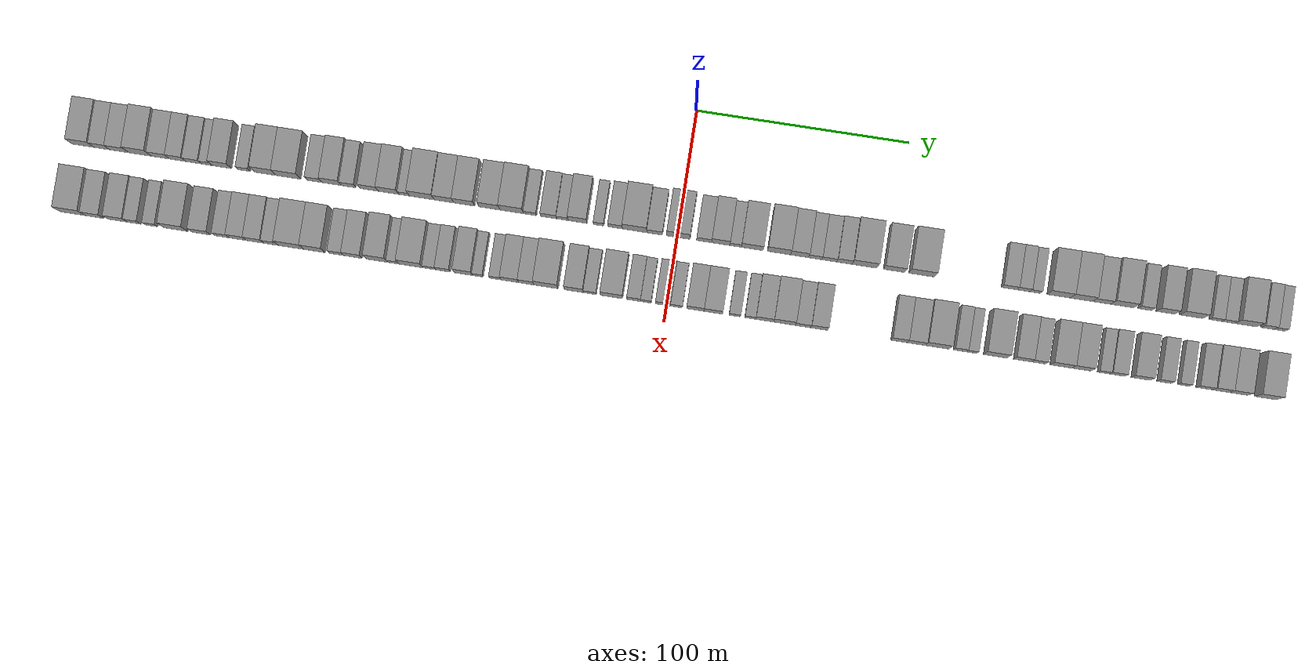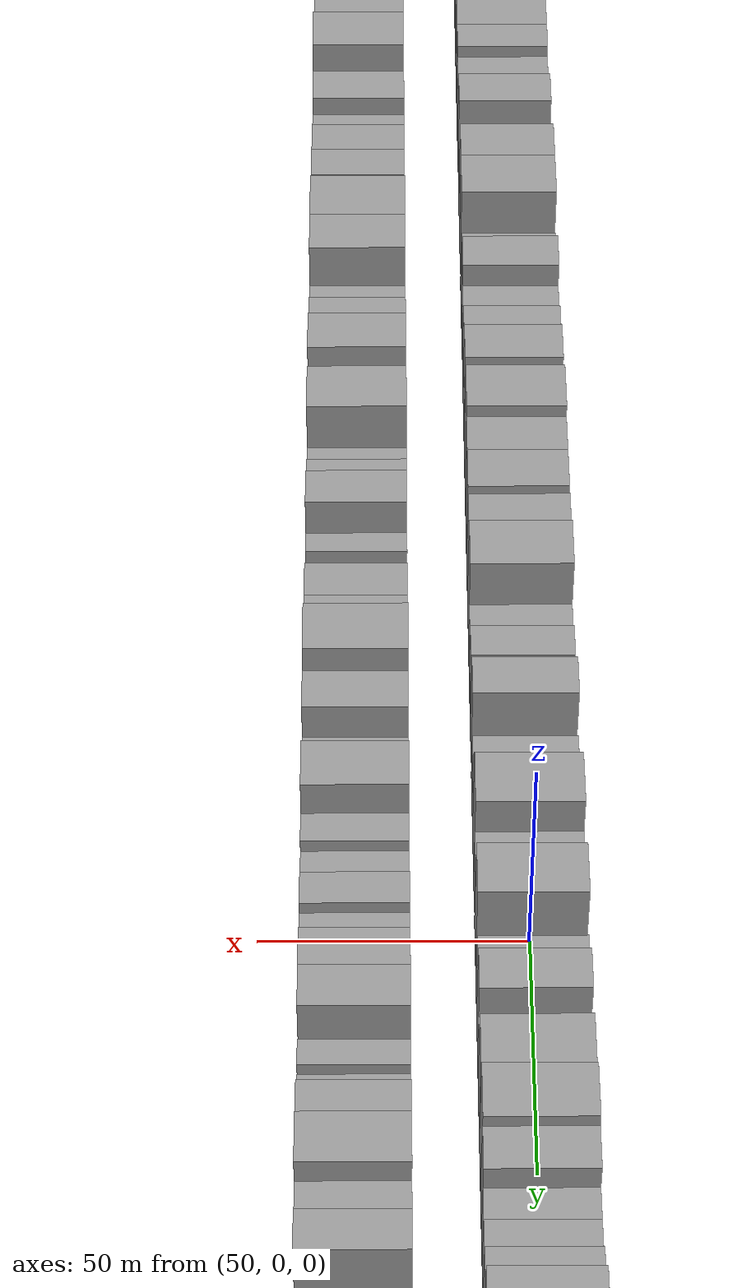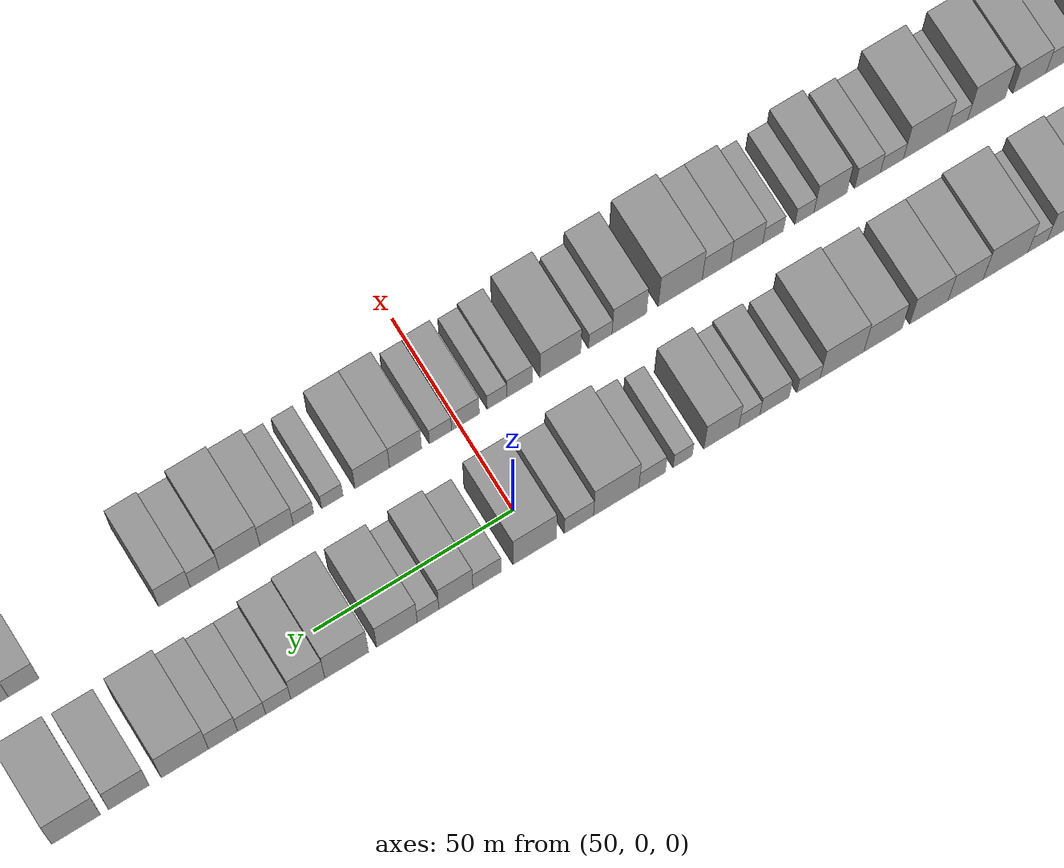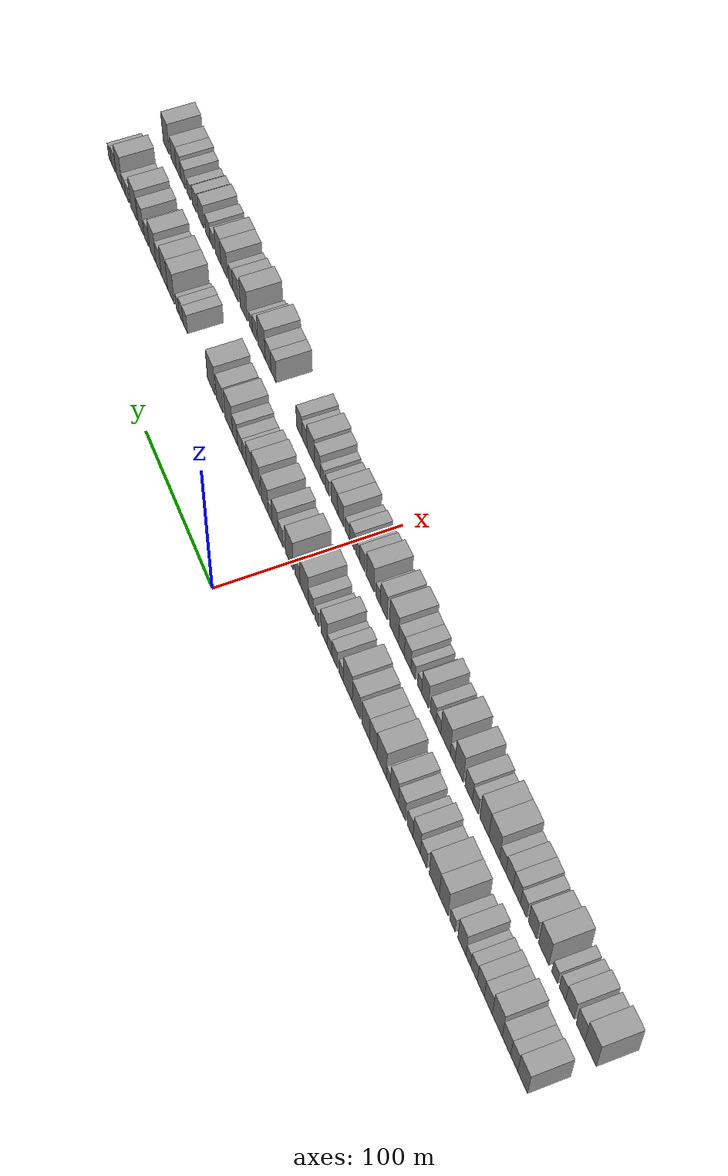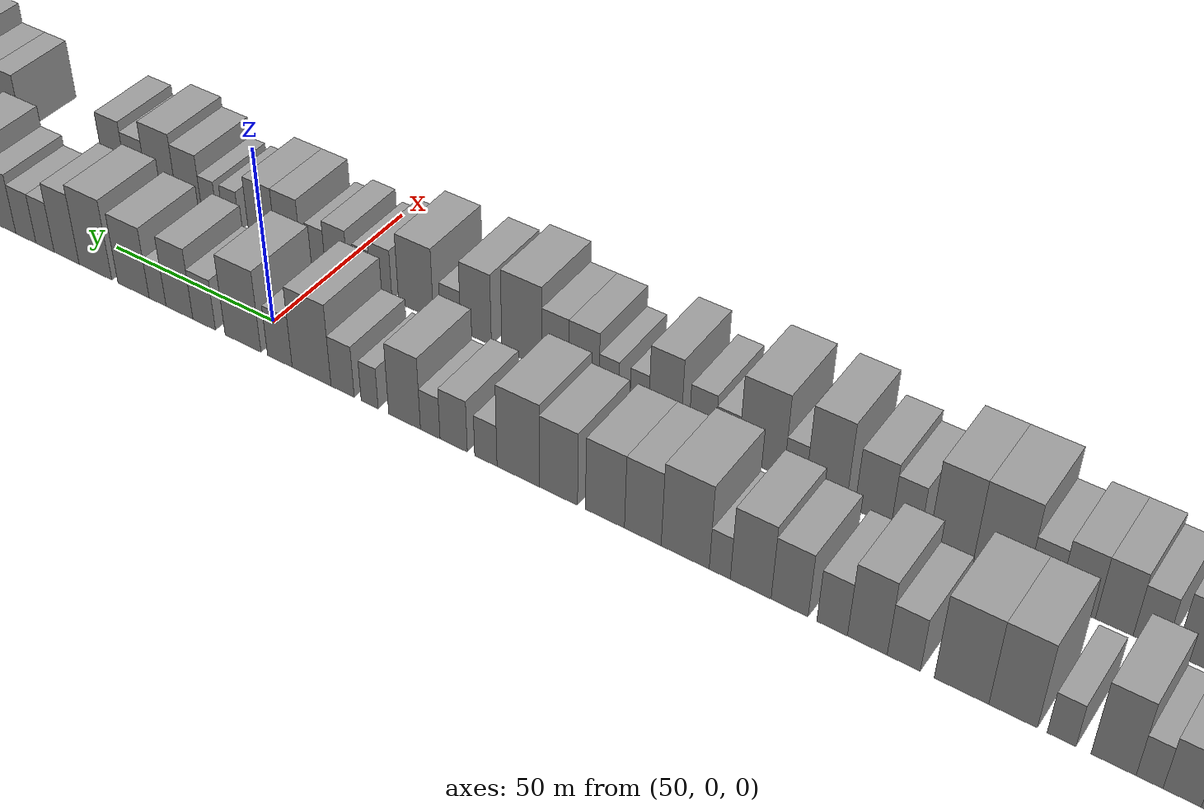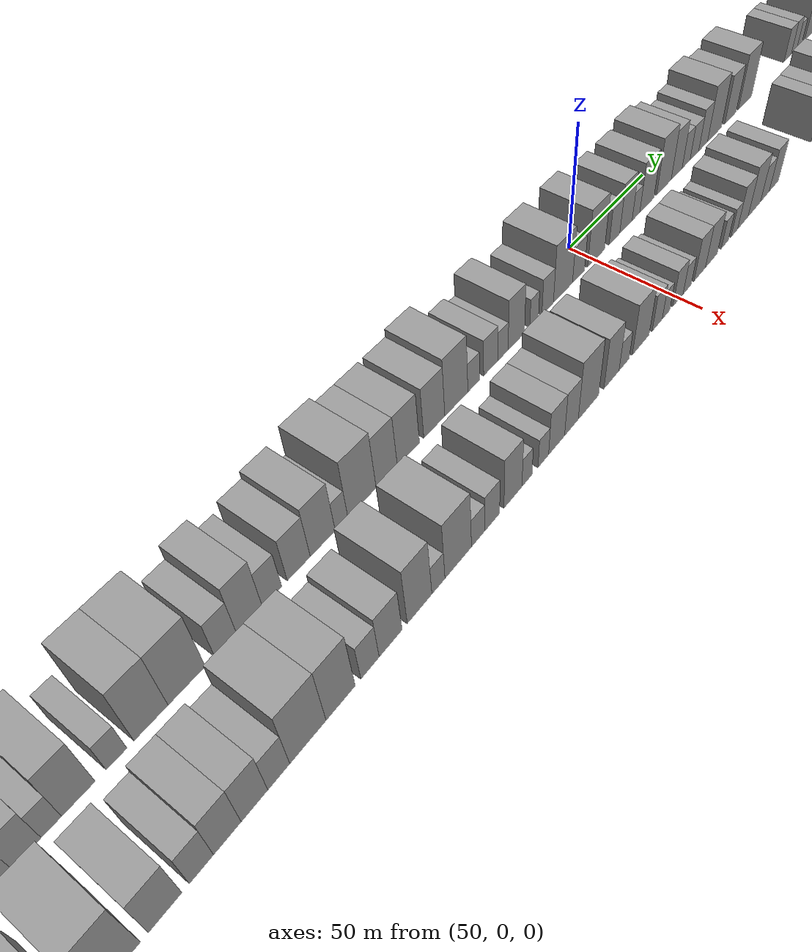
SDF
<sdf version="1.6">
 <world name="default">
  <scene>
   <sky><clouds><speed>12</speed></clouds></sky>
   <ambient>0.4 0.4 0.4 1</ambient>
   <background>0.7 0.7 0.7 1</background>
   <shadows>1</shadows>
  </scene>
  <gravity>0 0 -9.8066</gravity>
  <magnetic_field>6e-06 2.3e-05 -4.2e-05</magnetic_field>
  <physics default="0" name="default_physics" type="ode">
   <ode>
    <solver>
     <type>quick</type>
     <iters>10</iters>
     <sor>1.0</sor>
     <use_dynamic_moi_rescaling>0</use_dynamic_moi_rescaling>
    </solver>
    <constraints>
     <cfm>0</cfm>
     <erp>0.2</erp>
     <contact_max_correcting_vel>100</contact_max_correcting_vel>
     <contact_surface_layer>0.001</contact_surface_layer>
    </constraints>
   </ode>
   <max_step_size>0.004</max_step_size>
   <real_time_factor>1</real_time_factor>
   <real_time_update_rate>250</real_time_update_rate>
  </physics>
  <light name="sun" type="directional">
   <pose>0 0 10 0 0 0</pose>
   <diffuse>0.8 0.8 0.8 1</diffuse>
   <specular>0.2 0.2 0.2 1</specular>
   <attenuation>
    <range>1000</range>
    <constant>0.9</constant>
    <linear>0.01</linear>
    <quadratic>0.001</quadratic>
   </attenuation>
   <direction>-0.5 0.1 -0.9</direction>
  </light>
  <model name="building_1">
   <static>1</static>
   <pose>50.0000 -278.9319 0 0.000000 0.000000 0.000000</pose>
   <link name="link">
    <pose>0 0 10.50 0 0 0</pose>
    <collision name="collision"><geometry><box><size>20.0000 10.1363 21.0000</size></box></geometry></collision>
    <visual name="visual">
     <cast_shadows>0</cast_shadows>
     <geometry><box><size>20.0000 10.1363 21.0000</size></box></geometry>
     <material>
      <script>
       <uri>model://grey_wall/materials/scripts</uri>
       <uri>model://grey_wall/materials/textures</uri>
       <name>vrc/grey_wall</name>
      </script>
     </material>
    </visual>
   </link>
  </model>
  <model name="building_2">
   <static>1</static>
   <pose>50.0000 -270.0899 0 0.000000 0.000000 0.000000</pose>
   <link name="link">
    <pose>0 0 9.00 0 0 0</pose>
    <collision name="collision"><geometry><box><size>20.0000 7.5476 18.0000</size></box></geometry></collision>
    <visual name="visual">
     <cast_shadows>0</cast_shadows>
     <geometry><box><size>20.0000 7.5476 18.0000</size></box></geometry>
     <material>
      <script>
       <uri>model://grey_wall/materials/scripts</uri>
       <uri>model://grey_wall/materials/textures</uri>
       <name>vrc/grey_wall</name>
      </script>
     </material>
    </visual>
   </link>
  </model>
  <model name="building_3">
   <static>1</static>
   <pose>50.0000 -261.8540 0 0.000000 0.000000 0.000000</pose>
   <link name="link">
    <pose>0 0 9.00 0 0 0</pose>
    <collision name="collision"><geometry><box><size>20.0000 8.9242 18.0000</size></box></geometry></collision>
    <visual name="visual">
     <cast_shadows>0</cast_shadows>
     <geometry><box><size>20.0000 8.9242 18.0000</size></box></geometry>
     <material>
      <script>
       <uri>model://grey_wall/materials/scripts</uri>
       <uri>model://grey_wall/materials/textures</uri>
       <name>vrc/grey_wall</name>
      </script>
     </material>
    </visual>
   </link>
  </model>
  <model name="building_4">
   <static>1</static>
   <pose>50.0000 -252.0789 0 0.000000 0.000000 0.000000</pose>
   <link name="link">
    <pose>0 0 12.00 0 0 0</pose>
    <collision name="collision"><geometry><box><size>20.0000 10.6259 24.0000</size></box></geometry></collision>
    <visual name="visual">
     <cast_shadows>0</cast_shadows>
     <geometry><box><size>20.0000 10.6259 24.0000</size></box></geometry>
     <material>
      <script>
       <uri>model://grey_wall/materials/scripts</uri>
       <uri>model://grey_wall/materials/textures</uri>
       <name>vrc/grey_wall</name>
      </script>
     </material>
    </visual>
   </link>
  </model>
  <model name="building_5">
   <static>1</static>
   <pose>50.0000 -242.4415 0 0.000000 0.000000 0.000000</pose>
   <link name="link">
    <pose>0 0 9.00 0 0 0</pose>
    <collision name="collision"><geometry><box><size>20.0000 8.6490 18.0000</size></box></geometry></collision>
    <visual name="visual">
     <cast_shadows>0</cast_shadows>
     <geometry><box><size>20.0000 8.6490 18.0000</size></box></geometry>
     <material>
      <script>
       <uri>model://grey_wall/materials/scripts</uri>
       <uri>model://grey_wall/materials/textures</uri>
       <name>vrc/grey_wall</name>
      </script>
     </material>
    </visual>
   </link>
  </model>
  <model name="building_6">
   <static>1</static>
   <pose>50.0000 -234.3354 0 0.000000 0.000000 0.000000</pose>
   <link name="link">
    <pose>0 0 9.00 0 0 0</pose>
    <collision name="collision"><geometry><box><size>20.0000 7.5632 18.0000</size></box></geometry></collision>
    <visual name="visual">
     <cast_shadows>0</cast_shadows>
     <geometry><box><size>20.0000 7.5632 18.0000</size></box></geometry>
     <material>
      <script>
       <uri>model://grey_wall/materials/scripts</uri>
       <uri>model://grey_wall/materials/textures</uri>
       <name>vrc/grey_wall</name>
      </script>
     </material>
    </visual>
   </link>
  </model>
  <model name="building_7">
   <static>1</static>
   <pose>50.0000 -226.8695 0 0.000000 0.000000 0.000000</pose>
   <link name="link">
    <pose>0 0 7.50 0 0 0</pose>
    <collision name="collision"><geometry><box><size>20.0000 7.3687 15.0000</size></box></geometry></collision>
    <visual name="visual">
     <cast_shadows>0</cast_shadows>
     <geometry><box><size>20.0000 7.3687 15.0000</size></box></geometry>
     <material>
      <script>
       <uri>model://grey_wall/materials/scripts</uri>
       <uri>model://grey_wall/materials/textures</uri>
       <name>vrc/grey_wall</name>
      </script>
     </material>
    </visual>
   </link>
  </model>
  <model name="building_8">
   <static>1</static>
   <pose>50.0000 -220.5468 0 0.000000 0.000000 0.000000</pose>
   <link name="link">
    <pose>0 0 6.00 0 0 0</pose>
    <collision name="collision"><geometry><box><size>20.0000 5.2767 12.0000</size></box></geometry></collision>
    <visual name="visual">
     <cast_shadows>0</cast_shadows>
     <geometry><box><size>20.0000 5.2767 12.0000</size></box></geometry>
     <material>
      <script>
       <uri>model://grey_wall/materials/scripts</uri>
       <uri>model://grey_wall/materials/textures</uri>
       <name>vrc/grey_wall</name>
      </script>
     </material>
    </visual>
   </link>
  </model>
  <model name="building_9">
   <static>1</static>
   <pose>50.0000 -213.4401 0 0.000000 0.000000 0.000000</pose>
   <link name="link">
    <pose>0 0 10.50 0 0 0</pose>
    <collision name="collision"><geometry><box><size>20.0000 8.9366 21.0000</size></box></geometry></collision>
    <visual name="visual">
     <cast_shadows>0</cast_shadows>
     <geometry><box><size>20.0000 8.9366 21.0000</size></box></geometry>
     <material>
      <script>
       <uri>model://grey_wall/materials/scripts</uri>
       <uri>model://grey_wall/materials/textures</uri>
       <name>vrc/grey_wall</name>
      </script>
     </material>
    </visual>
   </link>
  </model>
  <model name="building_10">
   <static>1</static>
   <pose>50.0000 -203.0445 0 0.000000 0.000000 0.000000</pose>
   <link name="link">
    <pose>0 0 6.00 0 0 0</pose>
    <collision name="collision"><geometry><box><size>20.0000 5.8547 12.0000</size></box></geometry></collision>
    <visual name="visual">
     <cast_shadows>0</cast_shadows>
     <geometry><box><size>20.0000 5.8547 12.0000</size></box></geometry>
     <material>
      <script>
       <uri>model://grey_wall/materials/scripts</uri>
       <uri>model://grey_wall/materials/textures</uri>
       <name>vrc/grey_wall</name>
      </script>
     </material>
    </visual>
   </link>
  </model>
  <model name="building_11">
   <static>1</static>
   <pose>50.0000 -193.0711 0 0.000000 0.000000 0.000000</pose>
   <link name="link">
    <pose>0 0 12.00 0 0 0</pose>
    <collision name="collision"><geometry><box><size>20.0000 10.0920 24.0000</size></box></geometry></collision>
    <visual name="visual">
     <cast_shadows>0</cast_shadows>
     <geometry><box><size>20.0000 10.0920 24.0000</size></box></geometry>
     <material>
      <script>
       <uri>model://grey_wall/materials/scripts</uri>
       <uri>model://grey_wall/materials/textures</uri>
       <name>vrc/grey_wall</name>
      </script>
     </material>
    </visual>
   </link>
  </model>
  <model name="building_12">
   <static>1</static>
   <pose>50.0000 -182.2278 0 0.000000 0.000000 0.000000</pose>
   <link name="link">
    <pose>0 0 12.00 0 0 0</pose>
    <collision name="collision"><geometry><box><size>20.0000 11.5945 24.0000</size></box></geometry></collision>
    <visual name="visual">
     <cast_shadows>0</cast_shadows>
     <geometry><box><size>20.0000 11.5945 24.0000</size></box></geometry>
     <material>
      <script>
       <uri>model://grey_wall/materials/scripts</uri>
       <uri>model://grey_wall/materials/textures</uri>
       <name>vrc/grey_wall</name>
      </script>
     </material>
    </visual>
   </link>
  </model>
  <model name="building_13">
   <static>1</static>
   <pose>50.0000 -169.8044 0 0.000000 0.000000 0.000000</pose>
   <link name="link">
    <pose>0 0 7.50 0 0 0</pose>
    <collision name="collision"><geometry><box><size>20.0000 7.2523 15.0000</size></box></geometry></collision>
    <visual name="visual">
     <cast_shadows>0</cast_shadows>
     <geometry><box><size>20.0000 7.2523 15.0000</size></box></geometry>
     <material>
      <script>
       <uri>model://grey_wall/materials/scripts</uri>
       <uri>model://grey_wall/materials/textures</uri>
       <name>vrc/grey_wall</name>
      </script>
     </material>
    </visual>
   </link>
  </model>
  <model name="building_14">
   <static>1</static>
   <pose>50.0000 -161.7620 0 0.000000 0.000000 0.000000</pose>
   <link name="link">
    <pose>0 0 10.50 0 0 0</pose>
    <collision name="collision"><geometry><box><size>20.0000 8.8325 21.0000</size></box></geometry></collision>
    <visual name="visual">
     <cast_shadows>0</cast_shadows>
     <geometry><box><size>20.0000 8.8325 21.0000</size></box></geometry>
     <material>
      <script>
       <uri>model://grey_wall/materials/scripts</uri>
       <uri>model://grey_wall/materials/textures</uri>
       <name>vrc/grey_wall</name>
      </script>
     </material>
    </visual>
   </link>
  </model>
  <model name="building_15">
   <static>1</static>
   <pose>50.0000 -153.9001 0 0.000000 0.000000 0.000000</pose>
   <link name="link">
    <pose>0 0 7.50 0 0 0</pose>
    <collision name="collision"><geometry><box><size>20.0000 6.8913 15.0000</size></box></geometry></collision>
    <visual name="visual">
     <cast_shadows>0</cast_shadows>
     <geometry><box><size>20.0000 6.8913 15.0000</size></box></geometry>
     <material>
      <script>
       <uri>model://grey_wall/materials/scripts</uri>
       <uri>model://grey_wall/materials/textures</uri>
       <name>vrc/grey_wall</name>
      </script>
     </material>
    </visual>
   </link>
  </model>
  <model name="building_16">
   <static>1</static>
   <pose>50.0000 -144.1862 0 0.000000 0.000000 0.000000</pose>
   <link name="link">
    <pose>0 0 9.00 0 0 0</pose>
    <collision name="collision"><geometry><box><size>20.0000 8.5365 18.0000</size></box></geometry></collision>
    <visual name="visual">
     <cast_shadows>0</cast_shadows>
     <geometry><box><size>20.0000 8.5365 18.0000</size></box></geometry>
     <material>
      <script>
       <uri>model://grey_wall/materials/scripts</uri>
       <uri>model://grey_wall/materials/textures</uri>
       <name>vrc/grey_wall</name>
      </script>
     </material>
    </visual>
   </link>
  </model>
  <model name="building_17">
   <static>1</static>
   <pose>50.0000 -135.1311 0 0.000000 0.000000 0.000000</pose>
   <link name="link">
    <pose>0 0 10.50 0 0 0</pose>
    <collision name="collision"><geometry><box><size>20.0000 9.5737 21.0000</size></box></geometry></collision>
    <visual name="visual">
     <cast_shadows>0</cast_shadows>
     <geometry><box><size>20.0000 9.5737 21.0000</size></box></geometry>
     <material>
      <script>
       <uri>model://grey_wall/materials/scripts</uri>
       <uri>model://grey_wall/materials/textures</uri>
       <name>vrc/grey_wall</name>
      </script>
     </material>
    </visual>
   </link>
  </model>
  <model name="building_18">
   <static>1</static>
   <pose>50.0000 -127.8326 0 0.000000 0.000000 0.000000</pose>
   <link name="link">
    <pose>0 0 6.00 0 0 0</pose>
    <collision name="collision"><geometry><box><size>20.0000 5.0233 12.0000</size></box></geometry></collision>
    <visual name="visual">
     <cast_shadows>0</cast_shadows>
     <geometry><box><size>20.0000 5.0233 12.0000</size></box></geometry>
     <material>
      <script>
       <uri>model://grey_wall/materials/scripts</uri>
       <uri>model://grey_wall/materials/textures</uri>
       <name>vrc/grey_wall</name>
      </script>
     </material>
    </visual>
   </link>
  </model>
  <model name="building_19">
   <static>1</static>
   <pose>50.0000 -119.4954 0 0.000000 0.000000 0.000000</pose>
   <link name="link">
    <pose>0 0 12.00 0 0 0</pose>
    <collision name="collision"><geometry><box><size>20.0000 11.6512 24.0000</size></box></geometry></collision>
    <visual name="visual">
     <cast_shadows>0</cast_shadows>
     <geometry><box><size>20.0000 11.6512 24.0000</size></box></geometry>
     <material>
      <script>
       <uri>model://grey_wall/materials/scripts</uri>
       <uri>model://grey_wall/materials/textures</uri>
       <name>vrc/grey_wall</name>
      </script>
     </material>
    </visual>
   </link>
  </model>
  <model name="building_20">
   <static>1</static>
   <pose>50.0000 -109.1221 0 0.000000 0.000000 0.000000</pose>
   <link name="link">
    <pose>0 0 10.50 0 0 0</pose>
    <collision name="collision"><geometry><box><size>20.0000 9.0954 21.0000</size></box></geometry></collision>
    <visual name="visual">
     <cast_shadows>0</cast_shadows>
     <geometry><box><size>20.0000 9.0954 21.0000</size></box></geometry>
     <material>
      <script>
       <uri>model://grey_wall/materials/scripts</uri>
       <uri>model://grey_wall/materials/textures</uri>
       <name>vrc/grey_wall</name>
      </script>
     </material>
    </visual>
   </link>
  </model>
  <model name="building_21">
   <static>1</static>
   <pose>50.0000 -99.6407 0 0.000000 0.000000 0.000000</pose>
   <link name="link">
    <pose>0 0 10.50 0 0 0</pose>
    <collision name="collision"><geometry><box><size>20.0000 9.8675 21.0000</size></box></geometry></collision>
    <visual name="visual">
     <cast_shadows>0</cast_shadows>
     <geometry><box><size>20.0000 9.8675 21.0000</size></box></geometry>
     <material>
      <script>
       <uri>model://grey_wall/materials/scripts</uri>
       <uri>model://grey_wall/materials/textures</uri>
       <name>vrc/grey_wall</name>
      </script>
     </material>
    </visual>
   </link>
  </model>
  <model name="building_22">
   <static>1</static>
   <pose>50.0000 -87.7980 0 0.000000 0.000000 0.000000</pose>
   <link name="link">
    <pose>0 0 10.50 0 0 0</pose>
    <collision name="collision"><geometry><box><size>20.0000 9.8178 21.0000</size></box></geometry></collision>
    <visual name="visual">
     <cast_shadows>0</cast_shadows>
     <geometry><box><size>20.0000 9.8178 21.0000</size></box></geometry>
     <material>
      <script>
       <uri>model://grey_wall/materials/scripts</uri>
       <uri>model://grey_wall/materials/textures</uri>
       <name>vrc/grey_wall</name>
      </script>
     </material>
    </visual>
   </link>
  </model>
  <model name="building_23">
   <static>1</static>
   <pose>50.0000 -77.2852 0 0.000000 0.000000 0.000000</pose>
   <link name="link">
    <pose>0 0 12.00 0 0 0</pose>
    <collision name="collision"><geometry><box><size>20.0000 11.2078 24.0000</size></box></geometry></collision>
    <visual name="visual">
     <cast_shadows>0</cast_shadows>
     <geometry><box><size>20.0000 11.2078 24.0000</size></box></geometry>
     <material>
      <script>
       <uri>model://grey_wall/materials/scripts</uri>
       <uri>model://grey_wall/materials/textures</uri>
       <name>vrc/grey_wall</name>
      </script>
     </material>
    </visual>
   </link>
  </model>
  <model name="building_24">
   <static>1</static>
   <pose>50.0000 -68.6890 0 0.000000 0.000000 0.000000</pose>
   <link name="link">
    <pose>0 0 6.00 0 0 0</pose>
    <collision name="collision"><geometry><box><size>20.0000 5.9847 12.0000</size></box></geometry></collision>
    <visual name="visual">
     <cast_shadows>0</cast_shadows>
     <geometry><box><size>20.0000 5.9847 12.0000</size></box></geometry>
     <material>
      <script>
       <uri>model://grey_wall/materials/scripts</uri>
       <uri>model://grey_wall/materials/textures</uri>
       <name>vrc/grey_wall</name>
      </script>
     </material>
    </visual>
   </link>
  </model>
  <model name="building_25">
   <static>1</static>
   <pose>50.0000 -59.9812 0 0.000000 0.000000 0.000000</pose>
   <link name="link">
    <pose>0 0 7.50 0 0 0</pose>
    <collision name="collision"><geometry><box><size>20.0000 7.4309 15.0000</size></box></geometry></collision>
    <visual name="visual">
     <cast_shadows>0</cast_shadows>
     <geometry><box><size>20.0000 7.4309 15.0000</size></box></geometry>
     <material>
      <script>
       <uri>model://grey_wall/materials/scripts</uri>
       <uri>model://grey_wall/materials/textures</uri>
       <name>vrc/grey_wall</name>
      </script>
     </material>
    </visual>
   </link>
  </model>
  <model name="building_26">
   <static>1</static>
   <pose>50.0000 -53.5605 0 0.000000 0.000000 0.000000</pose>
   <link name="link">
    <pose>0 0 6.00 0 0 0</pose>
    <collision name="collision"><geometry><box><size>20.0000 5.4105 12.0000</size></box></geometry></collision>
    <visual name="visual">
     <cast_shadows>0</cast_shadows>
     <geometry><box><size>20.0000 5.4105 12.0000</size></box></geometry>
     <material>
      <script>
       <uri>model://grey_wall/materials/scripts</uri>
       <uri>model://grey_wall/materials/textures</uri>
       <name>vrc/grey_wall</name>
      </script>
     </material>
    </visual>
   </link>
  </model>
  <model name="building_27">
   <static>1</static>
   <pose>50.0000 -46.4148 0 0.000000 0.000000 0.000000</pose>
   <link name="link">
    <pose>0 0 10.50 0 0 0</pose>
    <collision name="collision"><geometry><box><size>20.0000 8.8810 21.0000</size></box></geometry></collision>
    <visual name="visual">
     <cast_shadows>0</cast_shadows>
     <geometry><box><size>20.0000 8.8810 21.0000</size></box></geometry>
     <material>
      <script>
       <uri>model://grey_wall/materials/scripts</uri>
       <uri>model://grey_wall/materials/textures</uri>
       <name>vrc/grey_wall</name>
      </script>
     </material>
    </visual>
   </link>
  </model>
  <model name="building_28">
   <static>1</static>
   <pose>50.0000 -36.5562 0 0.000000 0.000000 0.000000</pose>
   <link name="link">
    <pose>0 0 6.00 0 0 0</pose>
    <collision name="collision"><geometry><box><size>20.0000 4.8362 12.0000</size></box></geometry></collision>
    <visual name="visual">
     <cast_shadows>0</cast_shadows>
     <geometry><box><size>20.0000 4.8362 12.0000</size></box></geometry>
     <material>
      <script>
       <uri>model://grey_wall/materials/scripts</uri>
       <uri>model://grey_wall/materials/textures</uri>
       <name>vrc/grey_wall</name>
      </script>
     </material>
    </visual>
   </link>
  </model>
  <model name="building_29">
   <static>1</static>
   <pose>50.0000 -28.7875 0 0.000000 0.000000 0.000000</pose>
   <link name="link">
    <pose>0 0 7.50 0 0 0</pose>
    <collision name="collision"><geometry><box><size>20.0000 6.7012 15.0000</size></box></geometry></collision>
    <visual name="visual">
     <cast_shadows>0</cast_shadows>
     <geometry><box><size>20.0000 6.7012 15.0000</size></box></geometry>
     <material>
      <script>
       <uri>model://grey_wall/materials/scripts</uri>
       <uri>model://grey_wall/materials/textures</uri>
       <name>vrc/grey_wall</name>
      </script>
     </material>
    </visual>
   </link>
  </model>
  <model name="building_30">
   <static>1</static>
   <pose>50.0000 -19.7157 0 0.000000 0.000000 0.000000</pose>
   <link name="link">
    <pose>0 0 12.00 0 0 0</pose>
    <collision name="collision"><geometry><box><size>20.0000 11.4425 24.0000</size></box></geometry></collision>
    <visual name="visual">
     <cast_shadows>0</cast_shadows>
     <geometry><box><size>20.0000 11.4425 24.0000</size></box></geometry>
     <material>
      <script>
       <uri>model://grey_wall/materials/scripts</uri>
       <uri>model://grey_wall/materials/textures</uri>
       <name>vrc/grey_wall</name>
      </script>
     </material>
    </visual>
   </link>
  </model>
  <model name="building_31">
   <static>1</static>
   <pose>50.0000 -10.3079 0 0.000000 0.000000 0.000000</pose>
   <link name="link">
    <pose>0 0 7.50 0 0 0</pose>
    <collision name="collision"><geometry><box><size>20.0000 7.3730 15.0000</size></box></geometry></collision>
    <visual name="visual">
     <cast_shadows>0</cast_shadows>
     <geometry><box><size>20.0000 7.3730 15.0000</size></box></geometry>
     <material>
      <script>
       <uri>model://grey_wall/materials/scripts</uri>
       <uri>model://grey_wall/materials/textures</uri>
       <name>vrc/grey_wall</name>
      </script>
     </material>
    </visual>
   </link>
  </model>
  <model name="building_32">
   <static>1</static>
   <pose>50.0000 0.8469 0 0.000000 0.000000 0.000000</pose>
   <link name="link">
    <pose>0 0 12.00 0 0 0</pose>
    <collision name="collision"><geometry><box><size>20.0000 10.9367 24.0000</size></box></geometry></collision>
    <visual name="visual">
     <cast_shadows>0</cast_shadows>
     <geometry><box><size>20.0000 10.9367 24.0000</size></box></geometry>
     <material>
      <script>
       <uri>model://grey_wall/materials/scripts</uri>
       <uri>model://grey_wall/materials/textures</uri>
       <name>vrc/grey_wall</name>
      </script>
     </material>
    </visual>
   </link>
  </model>
  <model name="building_33">
   <static>1</static>
   <pose>50.0000 12.8434 0 0.000000 0.000000 0.000000</pose>
   <link name="link">
    <pose>0 0 7.50 0 0 0</pose>
    <collision name="collision"><geometry><box><size>20.0000 7.0563 15.0000</size></box></geometry></collision>
    <visual name="visual">
     <cast_shadows>0</cast_shadows>
     <geometry><box><size>20.0000 7.0563 15.0000</size></box></geometry>
     <material>
      <script>
       <uri>model://grey_wall/materials/scripts</uri>
       <uri>model://grey_wall/materials/textures</uri>
       <name>vrc/grey_wall</name>
      </script>
     </material>
    </visual>
   </link>
  </model>
  <model name="building_34">
   <static>1</static>
   <pose>50.0000 20.6297 0 0.000000 0.000000 0.000000</pose>
   <link name="link">
    <pose>0 0 10.50 0 0 0</pose>
    <collision name="collision"><geometry><box><size>20.0000 8.5164 21.0000</size></box></geometry></collision>
    <visual name="visual">
     <cast_shadows>0</cast_shadows>
     <geometry><box><size>20.0000 8.5164 21.0000</size></box></geometry>
     <material>
      <script>
       <uri>model://grey_wall/materials/scripts</uri>
       <uri>model://grey_wall/materials/textures</uri>
       <name>vrc/grey_wall</name>
      </script>
     </material>
    </visual>
   </link>
  </model>
  <model name="building_35">
   <static>1</static>
   <pose>50.0000 27.5853 0 0.000000 0.000000 0.000000</pose>
   <link name="link">
    <pose>0 0 6.00 0 0 0</pose>
    <collision name="collision"><geometry><box><size>20.0000 5.3947 12.0000</size></box></geometry></collision>
    <visual name="visual">
     <cast_shadows>0</cast_shadows>
     <geometry><box><size>20.0000 5.3947 12.0000</size></box></geometry>
     <material>
      <script>
       <uri>model://grey_wall/materials/scripts</uri>
       <uri>model://grey_wall/materials/textures</uri>
       <name>vrc/grey_wall</name>
      </script>
     </material>
    </visual>
   </link>
  </model>
  <model name="building_36">
   <static>1</static>
   <pose>50.0000 35.3652 0 0.000000 0.000000 0.000000</pose>
   <link name="link">
    <pose>0 0 10.50 0 0 0</pose>
    <collision name="collision"><geometry><box><size>20.0000 10.1651 21.0000</size></box></geometry></collision>
    <visual name="visual">
     <cast_shadows>0</cast_shadows>
     <geometry><box><size>20.0000 10.1651 21.0000</size></box></geometry>
     <material>
      <script>
       <uri>model://grey_wall/materials/scripts</uri>
       <uri>model://grey_wall/materials/textures</uri>
       <name>vrc/grey_wall</name>
      </script>
     </material>
    </visual>
   </link>
  </model>
  <model name="building_37">
   <static>1</static>
   <pose>50.0000 47.8778 0 0.000000 0.000000 0.000000</pose>
   <link name="link">
    <pose>0 0 12.00 0 0 0</pose>
    <collision name="collision"><geometry><box><size>20.0000 10.8600 24.0000</size></box></geometry></collision>
    <visual name="visual">
     <cast_shadows>0</cast_shadows>
     <geometry><box><size>20.0000 10.8600 24.0000</size></box></geometry>
     <material>
      <script>
       <uri>model://grey_wall/materials/scripts</uri>
       <uri>model://grey_wall/materials/textures</uri>
       <name>vrc/grey_wall</name>
      </script>
     </material>
    </visual>
   </link>
  </model>
  <model name="building_38">
   <static>1</static>
   <pose>50.0000 57.5322 0 0.000000 0.000000 0.000000</pose>
   <link name="link">
    <pose>0 0 10.50 0 0 0</pose>
    <collision name="collision"><geometry><box><size>20.0000 8.4489 21.0000</size></box></geometry></collision>
    <visual name="visual">
     <cast_shadows>0</cast_shadows>
     <geometry><box><size>20.0000 8.4489 21.0000</size></box></geometry>
     <material>
      <script>
       <uri>model://grey_wall/materials/scripts</uri>
       <uri>model://grey_wall/materials/textures</uri>
       <name>vrc/grey_wall</name>
      </script>
     </material>
    </visual>
   </link>
  </model>
  <model name="building_39">
   <static>1</static>
   <pose>50.0000 64.8607 0 0.000000 0.000000 0.000000</pose>
   <link name="link">
    <pose>0 0 7.50 0 0 0</pose>
    <collision name="collision"><geometry><box><size>20.0000 6.2079 15.0000</size></box></geometry></collision>
    <visual name="visual">
     <cast_shadows>0</cast_shadows>
     <geometry><box><size>20.0000 6.2079 15.0000</size></box></geometry>
     <material>
      <script>
       <uri>model://grey_wall/materials/scripts</uri>
       <uri>model://grey_wall/materials/textures</uri>
       <name>vrc/grey_wall</name>
      </script>
     </material>
    </visual>
   </link>
  </model>
  <model name="building_40">
   <static>1</static>
   <pose>50.0000 71.4527 0 0.000000 0.000000 0.000000</pose>
   <link name="link">
    <pose>0 0 7.50 0 0 0</pose>
    <collision name="collision"><geometry><box><size>20.0000 6.9761 15.0000</size></box></geometry></collision>
    <visual name="visual">
     <cast_shadows>0</cast_shadows>
     <geometry><box><size>20.0000 6.9761 15.0000</size></box></geometry>
     <material>
      <script>
       <uri>model://grey_wall/materials/scripts</uri>
       <uri>model://grey_wall/materials/textures</uri>
       <name>vrc/grey_wall</name>
      </script>
     </material>
    </visual>
   </link>
  </model>
  <model name="building_41">
   <static>1</static>
   <pose>50.0000 78.5423 0 0.000000 0.000000 0.000000</pose>
   <link name="link">
    <pose>0 0 9.00 0 0 0</pose>
    <collision name="collision"><geometry><box><size>20.0000 7.2032 18.0000</size></box></geometry></collision>
    <visual name="visual">
     <cast_shadows>0</cast_shadows>
     <geometry><box><size>20.0000 7.2032 18.0000</size></box></geometry>
     <material>
      <script>
       <uri>model://grey_wall/materials/scripts</uri>
       <uri>model://grey_wall/materials/textures</uri>
       <name>vrc/grey_wall</name>
      </script>
     </material>
    </visual>
   </link>
  </model>
  <model name="building_42">
   <static>1</static>
   <pose>50.0000 87.9648 0 0.000000 0.000000 0.000000</pose>
   <link name="link">
    <pose>0 0 12.00 0 0 0</pose>
    <collision name="collision"><geometry><box><size>20.0000 11.6419 24.0000</size></box></geometry></collision>
    <visual name="visual">
     <cast_shadows>0</cast_shadows>
     <geometry><box><size>20.0000 11.6419 24.0000</size></box></geometry>
     <material>
      <script>
       <uri>model://grey_wall/materials/scripts</uri>
       <uri>model://grey_wall/materials/textures</uri>
       <name>vrc/grey_wall</name>
      </script>
     </material>
    </visual>
   </link>
  </model>
  <model name="building_43">
   <static>1</static>
   <pose>50.0000 101.7564 0 0.000000 0.000000 0.000000</pose>
   <link name="link">
    <pose>0 0 10.50 0 0 0</pose>
    <collision name="collision"><geometry><box><size>20.0000 9.9412 21.0000</size></box></geometry></collision>
    <visual name="visual">
     <cast_shadows>0</cast_shadows>
     <geometry><box><size>20.0000 9.9412 21.0000</size></box></geometry>
     <material>
      <script>
       <uri>model://grey_wall/materials/scripts</uri>
       <uri>model://grey_wall/materials/textures</uri>
       <name>vrc/grey_wall</name>
      </script>
     </material>
    </visual>
   </link>
  </model>
  <model name="building_44">
   <static>1</static>
   <pose>50.0000 114.7146 0 0.000000 0.000000 0.000000</pose>
   <link name="link">
    <pose>0 0 12.00 0 0 0</pose>
    <collision name="collision"><geometry><box><size>20.0000 11.9752 24.0000</size></box></geometry></collision>
    <visual name="visual">
     <cast_shadows>0</cast_shadows>
     <geometry><box><size>20.0000 11.9752 24.0000</size></box></geometry>
     <material>
      <script>
       <uri>model://grey_wall/materials/scripts</uri>
       <uri>model://grey_wall/materials/textures</uri>
       <name>vrc/grey_wall</name>
      </script>
     </material>
    </visual>
   </link>
  </model>
  <model name="building_45">
   <static>1</static>
   <pose>50.0000 155.5697 0 0.000000 0.000000 0.000000</pose>
   <link name="link">
    <pose>0 0 7.50 0 0 0</pose>
    <collision name="collision"><geometry><box><size>20.0000 7.2450 15.0000</size></box></geometry></collision>
    <visual name="visual">
     <cast_shadows>0</cast_shadows>
     <geometry><box><size>20.0000 7.2450 15.0000</size></box></geometry>
     <material>
      <script>
       <uri>model://grey_wall/materials/scripts</uri>
       <uri>model://grey_wall/materials/textures</uri>
       <name>vrc/grey_wall</name>
      </script>
     </material>
    </visual>
   </link>
  </model>
  <model name="building_46">
   <static>1</static>
   <pose>50.0000 162.2053 0 0.000000 0.000000 0.000000</pose>
   <link name="link">
    <pose>0 0 7.50 0 0 0</pose>
    <collision name="collision"><geometry><box><size>20.0000 6.0262 15.0000</size></box></geometry></collision>
    <visual name="visual">
     <cast_shadows>0</cast_shadows>
     <geometry><box><size>20.0000 6.0262 15.0000</size></box></geometry>
     <material>
      <script>
       <uri>model://grey_wall/materials/scripts</uri>
       <uri>model://grey_wall/materials/textures</uri>
       <name>vrc/grey_wall</name>
      </script>
     </material>
    </visual>
   </link>
  </model>
  <model name="building_47">
   <static>1</static>
   <pose>50.0000 167.7446 0 0.000000 0.000000 0.000000</pose>
   <link name="link">
    <pose>0 0 6.00 0 0 0</pose>
    <collision name="collision"><geometry><box><size>20.0000 5.0525 12.0000</size></box></geometry></collision>
    <visual name="visual">
     <cast_shadows>0</cast_shadows>
     <geometry><box><size>20.0000 5.0525 12.0000</size></box></geometry>
     <material>
      <script>
       <uri>model://grey_wall/materials/scripts</uri>
       <uri>model://grey_wall/materials/textures</uri>
       <name>vrc/grey_wall</name>
      </script>
     </material>
    </visual>
   </link>
  </model>
  <model name="building_48">
   <static>1</static>
   <pose>50.0000 178.7050 0 0.000000 0.000000 0.000000</pose>
   <link name="link">
    <pose>0 0 12.00 0 0 0</pose>
    <collision name="collision"><geometry><box><size>20.0000 10.8684 24.0000</size></box></geometry></collision>
    <visual name="visual">
     <cast_shadows>0</cast_shadows>
     <geometry><box><size>20.0000 10.8684 24.0000</size></box></geometry>
     <material>
      <script>
       <uri>model://grey_wall/materials/scripts</uri>
       <uri>model://grey_wall/materials/textures</uri>
       <name>vrc/grey_wall</name>
      </script>
     </material>
    </visual>
   </link>
  </model>
  <model name="building_49">
   <static>1</static>
   <pose>50.0000 189.3468 0 0.000000 0.000000 0.000000</pose>
   <link name="link">
    <pose>0 0 12.00 0 0 0</pose>
    <collision name="collision"><geometry><box><size>20.0000 10.4151 24.0000</size></box></geometry></collision>
    <visual name="visual">
     <cast_shadows>0</cast_shadows>
     <geometry><box><size>20.0000 10.4151 24.0000</size></box></geometry>
     <material>
      <script>
       <uri>model://grey_wall/materials/scripts</uri>
       <uri>model://grey_wall/materials/textures</uri>
       <name>vrc/grey_wall</name>
      </script>
     </material>
    </visual>
   </link>
  </model>
  <model name="building_50">
   <static>1</static>
   <pose>50.0000 198.8236 0 0.000000 0.000000 0.000000</pose>
   <link name="link">
    <pose>0 0 9.00 0 0 0</pose>
    <collision name="collision"><geometry><box><size>20.0000 8.5385 18.0000</size></box></geometry></collision>
    <visual name="visual">
     <cast_shadows>0</cast_shadows>
     <geometry><box><size>20.0000 8.5385 18.0000</size></box></geometry>
     <material>
      <script>
       <uri>model://grey_wall/materials/scripts</uri>
       <uri>model://grey_wall/materials/textures</uri>
       <name>vrc/grey_wall</name>
      </script>
     </material>
    </visual>
   </link>
  </model>
  <model name="building_51">
   <static>1</static>
   <pose>50.0000 208.4541 0 0.000000 0.000000 0.000000</pose>
   <link name="link">
    <pose>0 0 12.00 0 0 0</pose>
    <collision name="collision"><geometry><box><size>20.0000 10.7225 24.0000</size></box></geometry></collision>
    <visual name="visual">
     <cast_shadows>0</cast_shadows>
     <geometry><box><size>20.0000 10.7225 24.0000</size></box></geometry>
     <material>
      <script>
       <uri>model://grey_wall/materials/scripts</uri>
       <uri>model://grey_wall/materials/textures</uri>
       <name>vrc/grey_wall</name>
      </script>
     </material>
    </visual>
   </link>
  </model>
  <model name="building_52">
   <static>1</static>
   <pose>50.0000 219.0162 0 0.000000 0.000000 0.000000</pose>
   <link name="link">
    <pose>0 0 7.50 0 0 0</pose>
    <collision name="collision"><geometry><box><size>20.0000 6.4017 15.0000</size></box></geometry></collision>
    <visual name="visual">
     <cast_shadows>0</cast_shadows>
     <geometry><box><size>20.0000 6.4017 15.0000</size></box></geometry>
     <material>
      <script>
       <uri>model://grey_wall/materials/scripts</uri>
       <uri>model://grey_wall/materials/textures</uri>
       <name>vrc/grey_wall</name>
      </script>
     </material>
    </visual>
   </link>
  </model>
  <model name="building_53">
   <static>1</static>
   <pose>50.0000 228.6528 0 0.000000 0.000000 0.000000</pose>
   <link name="link">
    <pose>0 0 10.50 0 0 0</pose>
    <collision name="collision"><geometry><box><size>20.0000 8.8717 21.0000</size></box></geometry></collision>
    <visual name="visual">
     <cast_shadows>0</cast_shadows>
     <geometry><box><size>20.0000 8.8717 21.0000</size></box></geometry>
     <material>
      <script>
       <uri>model://grey_wall/materials/scripts</uri>
       <uri>model://grey_wall/materials/textures</uri>
       <name>vrc/grey_wall</name>
      </script>
     </material>
    </visual>
   </link>
  </model>
  <model name="building_54">
   <static>1</static>
   <pose>50.0000 240.5531 0 0.000000 0.000000 0.000000</pose>
   <link name="link">
    <pose>0 0 12.00 0 0 0</pose>
    <collision name="collision"><geometry><box><size>20.0000 10.9288 24.0000</size></box></geometry></collision>
    <visual name="visual">
     <cast_shadows>0</cast_shadows>
     <geometry><box><size>20.0000 10.9288 24.0000</size></box></geometry>
     <material>
      <script>
       <uri>model://grey_wall/materials/scripts</uri>
       <uri>model://grey_wall/materials/textures</uri>
       <name>vrc/grey_wall</name>
      </script>
     </material>
    </visual>
   </link>
  </model>
  <model name="building_55">
   <static>1</static>
   <pose>50.0000 251.9315 0 0.000000 0.000000 0.000000</pose>
   <link name="link">
    <pose>0 0 6.00 0 0 0</pose>
    <collision name="collision"><geometry><box><size>20.0000 5.8281 12.0000</size></box></geometry></collision>
    <visual name="visual">
     <cast_shadows>0</cast_shadows>
     <geometry><box><size>20.0000 5.8281 12.0000</size></box></geometry>
     <material>
      <script>
       <uri>model://grey_wall/materials/scripts</uri>
       <uri>model://grey_wall/materials/textures</uri>
       <name>vrc/grey_wall</name>
      </script>
     </material>
    </visual>
   </link>
  </model>
  <model name="building_56">
   <static>1</static>
   <pose>50.0000 257.8235 0 0.000000 0.000000 0.000000</pose>
   <link name="link">
    <pose>0 0 6.00 0 0 0</pose>
    <collision name="collision"><geometry><box><size>20.0000 5.9559 12.0000</size></box></geometry></collision>
    <visual name="visual">
     <cast_shadows>0</cast_shadows>
     <geometry><box><size>20.0000 5.9559 12.0000</size></box></geometry>
     <material>
      <script>
       <uri>model://grey_wall/materials/scripts</uri>
       <uri>model://grey_wall/materials/textures</uri>
       <name>vrc/grey_wall</name>
      </script>
     </material>
    </visual>
   </link>
  </model>
  <model name="building_57">
   <static>1</static>
   <pose>50.0000 266.0088 0 0.000000 0.000000 0.000000</pose>
   <link name="link">
    <pose>0 0 12.00 0 0 0</pose>
    <collision name="collision"><geometry><box><size>20.0000 10.4145 24.0000</size></box></geometry></collision>
    <visual name="visual">
     <cast_shadows>0</cast_shadows>
     <geometry><box><size>20.0000 10.4145 24.0000</size></box></geometry>
     <material>
      <script>
       <uri>model://grey_wall/materials/scripts</uri>
       <uri>model://grey_wall/materials/textures</uri>
       <name>vrc/grey_wall</name>
      </script>
     </material>
    </visual>
   </link>
  </model>
  <model name="building_58">
   <static>1</static>
   <pose>50.0000 276.2362 0 0.000000 0.000000 0.000000</pose>
   <link name="link">
    <pose>0 0 7.50 0 0 0</pose>
    <collision name="collision"><geometry><box><size>20.0000 6.0404 15.0000</size></box></geometry></collision>
    <visual name="visual">
     <cast_shadows>0</cast_shadows>
     <geometry><box><size>20.0000 6.0404 15.0000</size></box></geometry>
     <material>
      <script>
       <uri>model://grey_wall/materials/scripts</uri>
       <uri>model://grey_wall/materials/textures</uri>
       <name>vrc/grey_wall</name>
      </script>
     </material>
    </visual>
   </link>
  </model>
  <model name="building_59">
   <static>1</static>
   <pose>50.0000 281.8988 0 0.000000 0.000000 0.000000</pose>
   <link name="link">
    <pose>0 0 6.00 0 0 0</pose>
    <collision name="collision"><geometry><box><size>20.0000 5.2848 12.0000</size></box></geometry></collision>
    <visual name="visual">
     <cast_shadows>0</cast_shadows>
     <geometry><box><size>20.0000 5.2848 12.0000</size></box></geometry>
     <material>
      <script>
       <uri>model://grey_wall/materials/scripts</uri>
       <uri>model://grey_wall/materials/textures</uri>
       <name>vrc/grey_wall</name>
      </script>
     </material>
    </visual>
   </link>
  </model>
  <model name="building_60">
   <static>1</static>
   <pose>82.0000 -278.1218 0 0.000000 0.000000 0.000000</pose>
   <link name="link">
    <pose>0 0 12.00 0 0 0</pose>
    <collision name="collision"><geometry><box><size>20.0000 11.7565 24.0000</size></box></geometry></collision>
    <visual name="visual">
     <cast_shadows>0</cast_shadows>
     <geometry><box><size>20.0000 11.7565 24.0000</size></box></geometry>
     <material>
      <script>
       <uri>model://grey_wall/materials/scripts</uri>
       <uri>model://grey_wall/materials/textures</uri>
       <name>vrc/grey_wall</name>
      </script>
     </material>
    </visual>
   </link>
  </model>
  <model name="building_61">
   <static>1</static>
   <pose>82.0000 -267.9045 0 0.000000 0.000000 0.000000</pose>
   <link name="link">
    <pose>0 0 9.00 0 0 0</pose>
    <collision name="collision"><geometry><box><size>20.0000 8.6781 18.0000</size></box></geometry></collision>
    <visual name="visual">
     <cast_shadows>0</cast_shadows>
     <geometry><box><size>20.0000 8.6781 18.0000</size></box></geometry>
     <material>
      <script>
       <uri>model://grey_wall/materials/scripts</uri>
       <uri>model://grey_wall/materials/textures</uri>
       <name>vrc/grey_wall</name>
      </script>
     </material>
    </visual>
   </link>
  </model>
  <model name="building_62">
   <static>1</static>
   <pose>82.0000 -257.1049 0 0.000000 0.000000 0.000000</pose>
   <link name="link">
    <pose>0 0 9.00 0 0 0</pose>
    <collision name="collision"><geometry><box><size>20.0000 8.9211 18.0000</size></box></geometry></collision>
    <visual name="visual">
     <cast_shadows>0</cast_shadows>
     <geometry><box><size>20.0000 8.9211 18.0000</size></box></geometry>
     <material>
      <script>
       <uri>model://grey_wall/materials/scripts</uri>
       <uri>model://grey_wall/materials/textures</uri>
       <name>vrc/grey_wall</name>
      </script>
     </material>
    </visual>
   </link>
  </model>
  <model name="building_63">
   <static>1</static>
   <pose>82.0000 -249.4211 0 0.000000 0.000000 0.000000</pose>
   <link name="link">
    <pose>0 0 7.50 0 0 0</pose>
    <collision name="collision"><geometry><box><size>20.0000 6.4465 15.0000</size></box></geometry></collision>
    <visual name="visual">
     <cast_shadows>0</cast_shadows>
     <geometry><box><size>20.0000 6.4465 15.0000</size></box></geometry>
     <material>
      <script>
       <uri>model://grey_wall/materials/scripts</uri>
       <uri>model://grey_wall/materials/textures</uri>
       <name>vrc/grey_wall</name>
      </script>
     </material>
    </visual>
   </link>
  </model>
  <model name="building_64">
   <static>1</static>
   <pose>82.0000 -241.2479 0 0.000000 0.000000 0.000000</pose>
   <link name="link">
    <pose>0 0 6.00 0 0 0</pose>
    <collision name="collision"><geometry><box><size>20.0000 5.8999 12.0000</size></box></geometry></collision>
    <visual name="visual">
     <cast_shadows>0</cast_shadows>
     <geometry><box><size>20.0000 5.8999 12.0000</size></box></geometry>
     <material>
      <script>
       <uri>model://grey_wall/materials/scripts</uri>
       <uri>model://grey_wall/materials/textures</uri>
       <name>vrc/grey_wall</name>
      </script>
     </material>
    </visual>
   </link>
  </model>
  <model name="building_65">
   <static>1</static>
   <pose>82.0000 -229.7522 0 0.000000 0.000000 0.000000</pose>
   <link name="link">
    <pose>0 0 12.00 0 0 0</pose>
    <collision name="collision"><geometry><box><size>20.0000 11.0914 24.0000</size></box></geometry></collision>
    <visual name="visual">
     <cast_shadows>0</cast_shadows>
     <geometry><box><size>20.0000 11.0914 24.0000</size></box></geometry>
     <material>
      <script>
       <uri>model://grey_wall/materials/scripts</uri>
       <uri>model://grey_wall/materials/textures</uri>
       <name>vrc/grey_wall</name>
      </script>
     </material>
    </visual>
   </link>
  </model>
  <model name="building_66">
   <static>1</static>
   <pose>82.0000 -217.7758 0 0.000000 0.000000 0.000000</pose>
   <link name="link">
    <pose>0 0 9.00 0 0 0</pose>
    <collision name="collision"><geometry><box><size>20.0000 8.8615 18.0000</size></box></geometry></collision>
    <visual name="visual">
     <cast_shadows>0</cast_shadows>
     <geometry><box><size>20.0000 8.8615 18.0000</size></box></geometry>
     <material>
      <script>
       <uri>model://grey_wall/materials/scripts</uri>
       <uri>model://grey_wall/materials/textures</uri>
       <name>vrc/grey_wall</name>
      </script>
     </material>
    </visual>
   </link>
  </model>
  <model name="building_67">
   <static>1</static>
   <pose>82.0000 -207.9640 0 0.000000 0.000000 0.000000</pose>
   <link name="link">
    <pose>0 0 7.50 0 0 0</pose>
    <collision name="collision"><geometry><box><size>20.0000 6.7620 15.0000</size></box></geometry></collision>
    <visual name="visual">
     <cast_shadows>0</cast_shadows>
     <geometry><box><size>20.0000 6.7620 15.0000</size></box></geometry>
     <material>
      <script>
       <uri>model://grey_wall/materials/scripts</uri>
       <uri>model://grey_wall/materials/textures</uri>
       <name>vrc/grey_wall</name>
      </script>
     </material>
    </visual>
   </link>
  </model>
  <model name="building_68">
   <static>1</static>
   <pose>82.0000 -200.5835 0 0.000000 0.000000 0.000000</pose>
   <link name="link">
    <pose>0 0 9.00 0 0 0</pose>
    <collision name="collision"><geometry><box><size>20.0000 7.9990 18.0000</size></box></geometry></collision>
    <visual name="visual">
     <cast_shadows>0</cast_shadows>
     <geometry><box><size>20.0000 7.9990 18.0000</size></box></geometry>
     <material>
      <script>
       <uri>model://grey_wall/materials/scripts</uri>
       <uri>model://grey_wall/materials/textures</uri>
       <name>vrc/grey_wall</name>
      </script>
     </material>
    </visual>
   </link>
  </model>
  <model name="building_69">
   <static>1</static>
   <pose>82.0000 -192.5527 0 0.000000 0.000000 0.000000</pose>
   <link name="link">
    <pose>0 0 9.00 0 0 0</pose>
    <collision name="collision"><geometry><box><size>20.0000 8.0625 18.0000</size></box></geometry></collision>
    <visual name="visual">
     <cast_shadows>0</cast_shadows>
     <geometry><box><size>20.0000 8.0625 18.0000</size></box></geometry>
     <material>
      <script>
       <uri>model://grey_wall/materials/scripts</uri>
       <uri>model://grey_wall/materials/textures</uri>
       <name>vrc/grey_wall</name>
      </script>
     </material>
    </visual>
   </link>
  </model>
  <model name="building_70">
   <static>1</static>
   <pose>82.0000 -185.0785 0 0.000000 0.000000 0.000000</pose>
   <link name="link">
    <pose>0 0 7.50 0 0 0</pose>
    <collision name="collision"><geometry><box><size>20.0000 6.8859 15.0000</size></box></geometry></collision>
    <visual name="visual">
     <cast_shadows>0</cast_shadows>
     <geometry><box><size>20.0000 6.8859 15.0000</size></box></geometry>
     <material>
      <script>
       <uri>model://grey_wall/materials/scripts</uri>
       <uri>model://grey_wall/materials/textures</uri>
       <name>vrc/grey_wall</name>
      </script>
     </material>
    </visual>
   </link>
  </model>
  <model name="building_71">
   <static>1</static>
   <pose>82.0000 -175.6701 0 0.000000 0.000000 0.000000</pose>
   <link name="link">
    <pose>0 0 12.00 0 0 0</pose>
    <collision name="collision"><geometry><box><size>20.0000 11.9309 24.0000</size></box></geometry></collision>
    <visual name="visual">
     <cast_shadows>0</cast_shadows>
     <geometry><box><size>20.0000 11.9309 24.0000</size></box></geometry>
     <material>
      <script>
       <uri>model://grey_wall/materials/scripts</uri>
       <uri>model://grey_wall/materials/textures</uri>
       <name>vrc/grey_wall</name>
      </script>
     </material>
    </visual>
   </link>
  </model>
  <model name="building_72">
   <static>1</static>
   <pose>82.0000 -164.6478 0 0.000000 0.000000 0.000000</pose>
   <link name="link">
    <pose>0 0 12.00 0 0 0</pose>
    <collision name="collision"><geometry><box><size>20.0000 10.1138 24.0000</size></box></geometry></collision>
    <visual name="visual">
     <cast_shadows>0</cast_shadows>
     <geometry><box><size>20.0000 10.1138 24.0000</size></box></geometry>
     <material>
      <script>
       <uri>model://grey_wall/materials/scripts</uri>
       <uri>model://grey_wall/materials/textures</uri>
       <name>vrc/grey_wall</name>
      </script>
     </material>
    </visual>
   </link>
  </model>
  <model name="building_73">
   <static>1</static>
   <pose>82.0000 -154.2439 0 0.000000 0.000000 0.000000</pose>
   <link name="link">
    <pose>0 0 7.50 0 0 0</pose>
    <collision name="collision"><geometry><box><size>20.0000 6.6939 15.0000</size></box></geometry></collision>
    <visual name="visual">
     <cast_shadows>0</cast_shadows>
     <geometry><box><size>20.0000 6.6939 15.0000</size></box></geometry>
     <material>
      <script>
       <uri>model://grey_wall/materials/scripts</uri>
       <uri>model://grey_wall/materials/textures</uri>
       <name>vrc/grey_wall</name>
      </script>
     </material>
    </visual>
   </link>
  </model>
  <model name="building_74">
   <static>1</static>
   <pose>82.0000 -146.5614 0 0.000000 0.000000 0.000000</pose>
   <link name="link">
    <pose>0 0 9.00 0 0 0</pose>
    <collision name="collision"><geometry><box><size>20.0000 8.6710 18.0000</size></box></geometry></collision>
    <visual name="visual">
     <cast_shadows>0</cast_shadows>
     <geometry><box><size>20.0000 8.6710 18.0000</size></box></geometry>
     <material>
      <script>
       <uri>model://grey_wall/materials/scripts</uri>
       <uri>model://grey_wall/materials/textures</uri>
       <name>vrc/grey_wall</name>
      </script>
     </material>
    </visual>
   </link>
  </model>
  <model name="building_75">
   <static>1</static>
   <pose>82.0000 -135.3176 0 0.000000 0.000000 0.000000</pose>
   <link name="link">
    <pose>0 0 12.00 0 0 0</pose>
    <collision name="collision"><geometry><box><size>20.0000 9.8166 24.0000</size></box></geometry></collision>
    <visual name="visual">
     <cast_shadows>0</cast_shadows>
     <geometry><box><size>20.0000 9.8166 24.0000</size></box></geometry>
     <material>
      <script>
       <uri>model://grey_wall/materials/scripts</uri>
       <uri>model://grey_wall/materials/textures</uri>
       <name>vrc/grey_wall</name>
      </script>
     </material>
    </visual>
   </link>
  </model>
  <model name="building_76">
   <static>1</static>
   <pose>82.0000 -127.7190 0 0.000000 0.000000 0.000000</pose>
   <link name="link">
    <pose>0 0 6.00 0 0 0</pose>
    <collision name="collision"><geometry><box><size>20.0000 5.3807 12.0000</size></box></geometry></collision>
    <visual name="visual">
     <cast_shadows>0</cast_shadows>
     <geometry><box><size>20.0000 5.3807 12.0000</size></box></geometry>
     <material>
      <script>
       <uri>model://grey_wall/materials/scripts</uri>
       <uri>model://grey_wall/materials/textures</uri>
       <name>vrc/grey_wall</name>
      </script>
     </material>
    </visual>
   </link>
  </model>
  <model name="building_77">
   <static>1</static>
   <pose>82.0000 -119.3712 0 0.000000 0.000000 0.000000</pose>
   <link name="link">
    <pose>0 0 12.00 0 0 0</pose>
    <collision name="collision"><geometry><box><size>20.0000 11.3148 24.0000</size></box></geometry></collision>
    <visual name="visual">
     <cast_shadows>0</cast_shadows>
     <geometry><box><size>20.0000 11.3148 24.0000</size></box></geometry>
     <material>
      <script>
       <uri>model://grey_wall/materials/scripts</uri>
       <uri>model://grey_wall/materials/textures</uri>
       <name>vrc/grey_wall</name>
      </script>
     </material>
    </visual>
   </link>
  </model>
  <model name="building_78">
   <static>1</static>
   <pose>82.0000 -110.7311 0 0.000000 0.000000 0.000000</pose>
   <link name="link">
    <pose>0 0 6.00 0 0 0</pose>
    <collision name="collision"><geometry><box><size>20.0000 5.9654 12.0000</size></box></geometry></collision>
    <visual name="visual">
     <cast_shadows>0</cast_shadows>
     <geometry><box><size>20.0000 5.9654 12.0000</size></box></geometry>
     <material>
      <script>
       <uri>model://grey_wall/materials/scripts</uri>
       <uri>model://grey_wall/materials/textures</uri>
       <name>vrc/grey_wall</name>
      </script>
     </material>
    </visual>
   </link>
  </model>
  <model name="building_79">
   <static>1</static>
   <pose>82.0000 -104.3885 0 0.000000 0.000000 0.000000</pose>
   <link name="link">
    <pose>0 0 7.50 0 0 0</pose>
    <collision name="collision"><geometry><box><size>20.0000 6.7198 15.0000</size></box></geometry></collision>
    <visual name="visual">
     <cast_shadows>0</cast_shadows>
     <geometry><box><size>20.0000 6.7198 15.0000</size></box></geometry>
     <material>
      <script>
       <uri>model://grey_wall/materials/scripts</uri>
       <uri>model://grey_wall/materials/textures</uri>
       <name>vrc/grey_wall</name>
      </script>
     </material>
    </visual>
   </link>
  </model>
  <model name="building_80">
   <static>1</static>
   <pose>82.0000 -94.7712 0 0.000000 0.000000 0.000000</pose>
   <link name="link">
    <pose>0 0 10.50 0 0 0</pose>
    <collision name="collision"><geometry><box><size>20.0000 8.5149 21.0000</size></box></geometry></collision>
    <visual name="visual">
     <cast_shadows>0</cast_shadows>
     <geometry><box><size>20.0000 8.5149 21.0000</size></box></geometry>
     <material>
      <script>
       <uri>model://grey_wall/materials/scripts</uri>
       <uri>model://grey_wall/materials/textures</uri>
       <name>vrc/grey_wall</name>
      </script>
     </material>
    </visual>
   </link>
  </model>
  <model name="building_81">
   <static>1</static>
   <pose>82.0000 -88.0511 0 0.000000 0.000000 0.000000</pose>
   <link name="link">
    <pose>0 0 6.00 0 0 0</pose>
    <collision name="collision"><geometry><box><size>20.0000 4.9253 12.0000</size></box></geometry></collision>
    <visual name="visual">
     <cast_shadows>0</cast_shadows>
     <geometry><box><size>20.0000 4.9253 12.0000</size></box></geometry>
     <material>
      <script>
       <uri>model://grey_wall/materials/scripts</uri>
       <uri>model://grey_wall/materials/textures</uri>
       <name>vrc/grey_wall</name>
      </script>
     </material>
    </visual>
   </link>
  </model>
  <model name="building_82">
   <static>1</static>
   <pose>82.0000 -79.9479 0 0.000000 0.000000 0.000000</pose>
   <link name="link">
    <pose>0 0 6.00 0 0 0</pose>
    <collision name="collision"><geometry><box><size>20.0000 5.2811 12.0000</size></box></geometry></collision>
    <visual name="visual">
     <cast_shadows>0</cast_shadows>
     <geometry><box><size>20.0000 5.2811 12.0000</size></box></geometry>
     <material>
      <script>
       <uri>model://grey_wall/materials/scripts</uri>
       <uri>model://grey_wall/materials/textures</uri>
       <name>vrc/grey_wall</name>
      </script>
     </material>
    </visual>
   </link>
  </model>
  <model name="building_83">
   <static>1</static>
   <pose>82.0000 -73.1731 0 0.000000 0.000000 0.000000</pose>
   <link name="link">
    <pose>0 0 9.00 0 0 0</pose>
    <collision name="collision"><geometry><box><size>20.0000 8.2685 18.0000</size></box></geometry></collision>
    <visual name="visual">
     <cast_shadows>0</cast_shadows>
     <geometry><box><size>20.0000 8.2685 18.0000</size></box></geometry>
     <material>
      <script>
       <uri>model://grey_wall/materials/scripts</uri>
       <uri>model://grey_wall/materials/textures</uri>
       <name>vrc/grey_wall</name>
      </script>
     </material>
    </visual>
   </link>
  </model>
  <model name="building_84">
   <static>1</static>
   <pose>82.0000 -65.3909 0 0.000000 0.000000 0.000000</pose>
   <link name="link">
    <pose>0 0 9.00 0 0 0</pose>
    <collision name="collision"><geometry><box><size>20.0000 7.2960 18.0000</size></box></geometry></collision>
    <visual name="visual">
     <cast_shadows>0</cast_shadows>
     <geometry><box><size>20.0000 7.2960 18.0000</size></box></geometry>
     <material>
      <script>
       <uri>model://grey_wall/materials/scripts</uri>
       <uri>model://grey_wall/materials/textures</uri>
       <name>vrc/grey_wall</name>
      </script>
     </material>
    </visual>
   </link>
  </model>
  <model name="building_85">
   <static>1</static>
   <pose>82.0000 -56.0980 0 0.000000 0.000000 0.000000</pose>
   <link name="link">
    <pose>0 0 12.00 0 0 0</pose>
    <collision name="collision"><geometry><box><size>20.0000 11.2897 24.0000</size></box></geometry></collision>
    <visual name="visual">
     <cast_shadows>0</cast_shadows>
     <geometry><box><size>20.0000 11.2897 24.0000</size></box></geometry>
     <material>
      <script>
       <uri>model://grey_wall/materials/scripts</uri>
       <uri>model://grey_wall/materials/textures</uri>
       <name>vrc/grey_wall</name>
      </script>
     </material>
    </visual>
   </link>
  </model>
  <model name="building_86">
   <static>1</static>
   <pose>82.0000 -43.0546 0 0.000000 0.000000 0.000000</pose>
   <link name="link">
    <pose>0 0 10.50 0 0 0</pose>
    <collision name="collision"><geometry><box><size>20.0000 8.7971 21.0000</size></box></geometry></collision>
    <visual name="visual">
     <cast_shadows>0</cast_shadows>
     <geometry><box><size>20.0000 8.7971 21.0000</size></box></geometry>
     <material>
      <script>
       <uri>model://grey_wall/materials/scripts</uri>
       <uri>model://grey_wall/materials/textures</uri>
       <name>vrc/grey_wall</name>
      </script>
     </material>
    </visual>
   </link>
  </model>
  <model name="building_87">
   <static>1</static>
   <pose>82.0000 -35.6611 0 0.000000 0.000000 0.000000</pose>
   <link name="link">
    <pose>0 0 6.00 0 0 0</pose>
    <collision name="collision"><geometry><box><size>20.0000 5.9900 12.0000</size></box></geometry></collision>
    <visual name="visual">
     <cast_shadows>0</cast_shadows>
     <geometry><box><size>20.0000 5.9900 12.0000</size></box></geometry>
     <material>
      <script>
       <uri>model://grey_wall/materials/scripts</uri>
       <uri>model://grey_wall/materials/textures</uri>
       <name>vrc/grey_wall</name>
      </script>
     </material>
    </visual>
   </link>
  </model>
  <model name="building_88">
   <static>1</static>
   <pose>82.0000 -25.4842 0 0.000000 0.000000 0.000000</pose>
   <link name="link">
    <pose>0 0 10.50 0 0 0</pose>
    <collision name="collision"><geometry><box><size>20.0000 10.3637 21.0000</size></box></geometry></collision>
    <visual name="visual">
     <cast_shadows>0</cast_shadows>
     <geometry><box><size>20.0000 10.3637 21.0000</size></box></geometry>
     <material>
      <script>
       <uri>model://grey_wall/materials/scripts</uri>
       <uri>model://grey_wall/materials/textures</uri>
       <name>vrc/grey_wall</name>
      </script>
     </material>
    </visual>
   </link>
  </model>
  <model name="building_89">
   <static>1</static>
   <pose>82.0000 -15.0850 0 0.000000 0.000000 0.000000</pose>
   <link name="link">
    <pose>0 0 7.50 0 0 0</pose>
    <collision name="collision"><geometry><box><size>20.0000 6.4347 15.0000</size></box></geometry></collision>
    <visual name="visual">
     <cast_shadows>0</cast_shadows>
     <geometry><box><size>20.0000 6.4347 15.0000</size></box></geometry>
     <material>
      <script>
       <uri>model://grey_wall/materials/scripts</uri>
       <uri>model://grey_wall/materials/textures</uri>
       <name>vrc/grey_wall</name>
      </script>
     </material>
    </visual>
   </link>
  </model>
  <model name="building_90">
   <static>1</static>
   <pose>82.0000 -9.3966 0 0.000000 0.000000 0.000000</pose>
   <link name="link">
    <pose>0 0 6.00 0 0 0</pose>
    <collision name="collision"><geometry><box><size>20.0000 4.9423 12.0000</size></box></geometry></collision>
    <visual name="visual">
     <cast_shadows>0</cast_shadows>
     <geometry><box><size>20.0000 4.9423 12.0000</size></box></geometry>
     <material>
      <script>
       <uri>model://grey_wall/materials/scripts</uri>
       <uri>model://grey_wall/materials/textures</uri>
       <name>vrc/grey_wall</name>
      </script>
     </material>
    </visual>
   </link>
  </model>
  <model name="building_91">
   <static>1</static>
   <pose>82.0000 -1.4251 0 0.000000 0.000000 0.000000</pose>
   <link name="link">
    <pose>0 0 7.50 0 0 0</pose>
    <collision name="collision"><geometry><box><size>20.0000 7.0005 15.0000</size></box></geometry></collision>
    <visual name="visual">
     <cast_shadows>0</cast_shadows>
     <geometry><box><size>20.0000 7.0005 15.0000</size></box></geometry>
     <material>
      <script>
       <uri>model://grey_wall/materials/scripts</uri>
       <uri>model://grey_wall/materials/textures</uri>
       <name>vrc/grey_wall</name>
      </script>
     </material>
    </visual>
   </link>
  </model>
  <model name="building_92">
   <static>1</static>
   <pose>82.0000 4.8660 0 0.000000 0.000000 0.000000</pose>
   <link name="link">
    <pose>0 0 6.00 0 0 0</pose>
    <collision name="collision"><geometry><box><size>20.0000 5.5818 12.0000</size></box></geometry></collision>
    <visual name="visual">
     <cast_shadows>0</cast_shadows>
     <geometry><box><size>20.0000 5.5818 12.0000</size></box></geometry>
     <material>
      <script>
       <uri>model://grey_wall/materials/scripts</uri>
       <uri>model://grey_wall/materials/textures</uri>
       <name>vrc/grey_wall</name>
      </script>
     </material>
    </visual>
   </link>
  </model>
  <model name="building_93">
   <static>1</static>
   <pose>82.0000 13.6942 0 0.000000 0.000000 0.000000</pose>
   <link name="link">
    <pose>0 0 9.00 0 0 0</pose>
    <collision name="collision"><geometry><box><size>20.0000 8.0745 18.0000</size></box></geometry></collision>
    <visual name="visual">
     <cast_shadows>0</cast_shadows>
     <geometry><box><size>20.0000 8.0745 18.0000</size></box></geometry>
     <material>
      <script>
       <uri>model://grey_wall/materials/scripts</uri>
       <uri>model://grey_wall/materials/textures</uri>
       <name>vrc/grey_wall</name>
      </script>
     </material>
    </visual>
   </link>
  </model>
  <model name="building_94">
   <static>1</static>
   <pose>82.0000 22.0796 0 0.000000 0.000000 0.000000</pose>
   <link name="link">
    <pose>0 0 9.00 0 0 0</pose>
    <collision name="collision"><geometry><box><size>20.0000 8.6964 18.0000</size></box></geometry></collision>
    <visual name="visual">
     <cast_shadows>0</cast_shadows>
     <geometry><box><size>20.0000 8.6964 18.0000</size></box></geometry>
     <material>
      <script>
       <uri>model://grey_wall/materials/scripts</uri>
       <uri>model://grey_wall/materials/textures</uri>
       <name>vrc/grey_wall</name>
      </script>
     </material>
    </visual>
   </link>
  </model>
  <model name="building_95">
   <static>1</static>
   <pose>82.0000 32.1022 0 0.000000 0.000000 0.000000</pose>
   <link name="link">
    <pose>0 0 6.00 0 0 0</pose>
    <collision name="collision"><geometry><box><size>20.0000 5.3489 12.0000</size></box></geometry></collision>
    <visual name="visual">
     <cast_shadows>0</cast_shadows>
     <geometry><box><size>20.0000 5.3489 12.0000</size></box></geometry>
     <material>
      <script>
       <uri>model://grey_wall/materials/scripts</uri>
       <uri>model://grey_wall/materials/textures</uri>
       <name>vrc/grey_wall</name>
      </script>
     </material>
    </visual>
   </link>
  </model>
  <model name="building_96">
   <static>1</static>
   <pose>82.0000 39.3089 0 0.000000 0.000000 0.000000</pose>
   <link name="link">
    <pose>0 0 6.00 0 0 0</pose>
    <collision name="collision"><geometry><box><size>20.0000 5.0645 12.0000</size></box></geometry></collision>
    <visual name="visual">
     <cast_shadows>0</cast_shadows>
     <geometry><box><size>20.0000 5.0645 12.0000</size></box></geometry>
     <material>
      <script>
       <uri>model://grey_wall/materials/scripts</uri>
       <uri>model://grey_wall/materials/textures</uri>
       <name>vrc/grey_wall</name>
      </script>
     </material>
    </visual>
   </link>
  </model>
  <model name="building_97">
   <static>1</static>
   <pose>82.0000 46.0332 0 0.000000 0.000000 0.000000</pose>
   <link name="link">
    <pose>0 0 9.00 0 0 0</pose>
    <collision name="collision"><geometry><box><size>20.0000 8.3841 18.0000</size></box></geometry></collision>
    <visual name="visual">
     <cast_shadows>0</cast_shadows>
     <geometry><box><size>20.0000 8.3841 18.0000</size></box></geometry>
     <material>
      <script>
       <uri>model://grey_wall/materials/scripts</uri>
       <uri>model://grey_wall/materials/textures</uri>
       <name>vrc/grey_wall</name>
      </script>
     </material>
    </visual>
   </link>
  </model>
  <model name="building_98">
   <static>1</static>
   <pose>82.0000 55.2792 0 0.000000 0.000000 0.000000</pose>
   <link name="link">
    <pose>0 0 10.50 0 0 0</pose>
    <collision name="collision"><geometry><box><size>20.0000 10.1079 21.0000</size></box></geometry></collision>
    <visual name="visual">
     <cast_shadows>0</cast_shadows>
     <geometry><box><size>20.0000 10.1079 21.0000</size></box></geometry>
     <material>
      <script>
       <uri>model://grey_wall/materials/scripts</uri>
       <uri>model://grey_wall/materials/textures</uri>
       <name>vrc/grey_wall</name>
      </script>
     </material>
    </visual>
   </link>
  </model>
  <model name="building_99">
   <static>1</static>
   <pose>82.0000 63.9472 0 0.000000 0.000000 0.000000</pose>
   <link name="link">
    <pose>0 0 7.50 0 0 0</pose>
    <collision name="collision"><geometry><box><size>20.0000 7.2280 15.0000</size></box></geometry></collision>
    <visual name="visual">
     <cast_shadows>0</cast_shadows>
     <geometry><box><size>20.0000 7.2280 15.0000</size></box></geometry>
     <material>
      <script>
       <uri>model://grey_wall/materials/scripts</uri>
       <uri>model://grey_wall/materials/textures</uri>
       <name>vrc/grey_wall</name>
      </script>
     </material>
    </visual>
   </link>
  </model>
  <model name="building_100">
   <static>1</static>
   <pose>82.0000 71.5030 0 0.000000 0.000000 0.000000</pose>
   <link name="link">
    <pose>0 0 9.00 0 0 0</pose>
    <collision name="collision"><geometry><box><size>20.0000 7.8837 18.0000</size></box></geometry></collision>
    <visual name="visual">
     <cast_shadows>0</cast_shadows>
     <geometry><box><size>20.0000 7.8837 18.0000</size></box></geometry>
     <material>
      <script>
       <uri>model://grey_wall/materials/scripts</uri>
       <uri>model://grey_wall/materials/textures</uri>
       <name>vrc/grey_wall</name>
      </script>
     </material>
    </visual>
   </link>
  </model>
  <model name="building_101">
   <static>1</static>
   <pose>82.0000 108.8107 0 0.000000 0.000000 0.000000</pose>
   <link name="link">
    <pose>0 0 9.00 0 0 0</pose>
    <collision name="collision"><geometry><box><size>20.0000 7.5772 18.0000</size></box></geometry></collision>
    <visual name="visual">
     <cast_shadows>0</cast_shadows>
     <geometry><box><size>20.0000 7.5772 18.0000</size></box></geometry>
     <material>
      <script>
       <uri>model://grey_wall/materials/scripts</uri>
       <uri>model://grey_wall/materials/textures</uri>
       <name>vrc/grey_wall</name>
      </script>
     </material>
    </visual>
   </link>
  </model>
  <model name="building_102">
   <static>1</static>
   <pose>82.0000 116.8280 0 0.000000 0.000000 0.000000</pose>
   <link name="link">
    <pose>0 0 9.00 0 0 0</pose>
    <collision name="collision"><geometry><box><size>20.0000 8.4575 18.0000</size></box></geometry></collision>
    <visual name="visual">
     <cast_shadows>0</cast_shadows>
     <geometry><box><size>20.0000 8.4575 18.0000</size></box></geometry>
     <material>
      <script>
       <uri>model://grey_wall/materials/scripts</uri>
       <uri>model://grey_wall/materials/textures</uri>
       <name>vrc/grey_wall</name>
      </script>
     </material>
    </visual>
   </link>
  </model>
  <model name="building_103">
   <static>1</static>
   <pose>82.0000 126.6372 0 0.000000 0.000000 0.000000</pose>
   <link name="link">
    <pose>0 0 12.00 0 0 0</pose>
    <collision name="collision"><geometry><box><size>20.0000 11.1607 24.0000</size></box></geometry></collision>
    <visual name="visual">
     <cast_shadows>0</cast_shadows>
     <geometry><box><size>20.0000 11.1607 24.0000</size></box></geometry>
     <material>
      <script>
       <uri>model://grey_wall/materials/scripts</uri>
       <uri>model://grey_wall/materials/textures</uri>
       <name>vrc/grey_wall</name>
      </script>
     </material>
    </visual>
   </link>
  </model>
  <model name="building_104">
   <static>1</static>
   <pose>82.0000 137.2559 0 0.000000 0.000000 0.000000</pose>
   <link name="link">
    <pose>0 0 7.50 0 0 0</pose>
    <collision name="collision"><geometry><box><size>20.0000 6.0768 15.0000</size></box></geometry></collision>
    <visual name="visual">
     <cast_shadows>0</cast_shadows>
     <geometry><box><size>20.0000 6.0768 15.0000</size></box></geometry>
     <material>
      <script>
       <uri>model://grey_wall/materials/scripts</uri>
       <uri>model://grey_wall/materials/textures</uri>
       <name>vrc/grey_wall</name>
      </script>
     </material>
    </visual>
   </link>
  </model>
  <model name="building_105">
   <static>1</static>
   <pose>82.0000 142.7807 0 0.000000 0.000000 0.000000</pose>
   <link name="link">
    <pose>0 0 6.00 0 0 0</pose>
    <collision name="collision"><geometry><box><size>20.0000 4.9728 12.0000</size></box></geometry></collision>
    <visual name="visual">
     <cast_shadows>0</cast_shadows>
     <geometry><box><size>20.0000 4.9728 12.0000</size></box></geometry>
     <material>
      <script>
       <uri>model://grey_wall/materials/scripts</uri>
       <uri>model://grey_wall/materials/textures</uri>
       <name>vrc/grey_wall</name>
      </script>
     </material>
    </visual>
   </link>
  </model>
  <model name="building_106">
   <static>1</static>
   <pose>82.0000 153.7696 0 0.000000 0.000000 0.000000</pose>
   <link name="link">
    <pose>0 0 12.00 0 0 0</pose>
    <collision name="collision"><geometry><box><size>20.0000 11.0049 24.0000</size></box></geometry></collision>
    <visual name="visual">
     <cast_shadows>0</cast_shadows>
     <geometry><box><size>20.0000 11.0049 24.0000</size></box></geometry>
     <material>
      <script>
       <uri>model://grey_wall/materials/scripts</uri>
       <uri>model://grey_wall/materials/textures</uri>
       <name>vrc/grey_wall</name>
      </script>
     </material>
    </visual>
   </link>
  </model>
  <model name="building_107">
   <static>1</static>
   <pose>82.0000 166.4532 0 0.000000 0.000000 0.000000</pose>
   <link name="link">
    <pose>0 0 9.00 0 0 0</pose>
    <collision name="collision"><geometry><box><size>20.0000 8.3625 18.0000</size></box></geometry></collision>
    <visual name="visual">
     <cast_shadows>0</cast_shadows>
     <geometry><box><size>20.0000 8.3625 18.0000</size></box></geometry>
     <material>
      <script>
       <uri>model://grey_wall/materials/scripts</uri>
       <uri>model://grey_wall/materials/textures</uri>
       <name>vrc/grey_wall</name>
      </script>
     </material>
    </visual>
   </link>
  </model>
  <model name="building_108">
   <static>1</static>
   <pose>82.0000 173.9625 0 0.000000 0.000000 0.000000</pose>
   <link name="link">
    <pose>0 0 7.50 0 0 0</pose>
    <collision name="collision"><geometry><box><size>20.0000 6.6560 15.0000</size></box></geometry></collision>
    <visual name="visual">
     <cast_shadows>0</cast_shadows>
     <geometry><box><size>20.0000 6.6560 15.0000</size></box></geometry>
     <material>
      <script>
       <uri>model://grey_wall/materials/scripts</uri>
       <uri>model://grey_wall/materials/textures</uri>
       <name>vrc/grey_wall</name>
      </script>
     </material>
    </visual>
   </link>
  </model>
  <model name="building_109">
   <static>1</static>
   <pose>82.0000 184.3375 0 0.000000 0.000000 0.000000</pose>
   <link name="link">
    <pose>0 0 10.50 0 0 0</pose>
    <collision name="collision"><geometry><box><size>20.0000 10.0942 21.0000</size></box></geometry></collision>
    <visual name="visual">
     <cast_shadows>0</cast_shadows>
     <geometry><box><size>20.0000 10.0942 21.0000</size></box></geometry>
     <material>
      <script>
       <uri>model://grey_wall/materials/scripts</uri>
       <uri>model://grey_wall/materials/textures</uri>
       <name>vrc/grey_wall</name>
      </script>
     </material>
    </visual>
   </link>
  </model>
  <model name="building_110">
   <static>1</static>
   <pose>82.0000 193.8829 0 0.000000 0.000000 0.000000</pose>
   <link name="link">
    <pose>0 0 10.50 0 0 0</pose>
    <collision name="collision"><geometry><box><size>20.0000 8.9965 21.0000</size></box></geometry></collision>
    <visual name="visual">
     <cast_shadows>0</cast_shadows>
     <geometry><box><size>20.0000 8.9965 21.0000</size></box></geometry>
     <material>
      <script>
       <uri>model://grey_wall/materials/scripts</uri>
       <uri>model://grey_wall/materials/textures</uri>
       <name>vrc/grey_wall</name>
      </script>
     </material>
    </visual>
   </link>
  </model>
  <model name="building_111">
   <static>1</static>
   <pose>82.0000 204.1977 0 0.000000 0.000000 0.000000</pose>
   <link name="link">
    <pose>0 0 6.00 0 0 0</pose>
    <collision name="collision"><geometry><box><size>20.0000 5.6331 12.0000</size></box></geometry></collision>
    <visual name="visual">
     <cast_shadows>0</cast_shadows>
     <geometry><box><size>20.0000 5.6331 12.0000</size></box></geometry>
     <material>
      <script>
       <uri>model://grey_wall/materials/scripts</uri>
       <uri>model://grey_wall/materials/textures</uri>
       <name>vrc/grey_wall</name>
      </script>
     </material>
    </visual>
   </link>
  </model>
  <model name="building_112">
   <static>1</static>
   <pose>82.0000 210.5671 0 0.000000 0.000000 0.000000</pose>
   <link name="link">
    <pose>0 0 7.50 0 0 0</pose>
    <collision name="collision"><geometry><box><size>20.0000 7.1056 15.0000</size></box></geometry></collision>
    <visual name="visual">
     <cast_shadows>0</cast_shadows>
     <geometry><box><size>20.0000 7.1056 15.0000</size></box></geometry>
     <material>
      <script>
       <uri>model://grey_wall/materials/scripts</uri>
       <uri>model://grey_wall/materials/textures</uri>
       <name>vrc/grey_wall</name>
      </script>
     </material>
    </visual>
   </link>
  </model>
  <model name="building_113">
   <static>1</static>
   <pose>82.0000 221.6136 0 0.000000 0.000000 0.000000</pose>
   <link name="link">
    <pose>0 0 9.00 0 0 0</pose>
    <collision name="collision"><geometry><box><size>20.0000 8.9875 18.0000</size></box></geometry></collision>
    <visual name="visual">
     <cast_shadows>0</cast_shadows>
     <geometry><box><size>20.0000 8.9875 18.0000</size></box></geometry>
     <material>
      <script>
       <uri>model://grey_wall/materials/scripts</uri>
       <uri>model://grey_wall/materials/textures</uri>
       <name>vrc/grey_wall</name>
      </script>
     </material>
    </visual>
   </link>
  </model>
  <model name="building_114">
   <static>1</static>
   <pose>82.0000 232.4111 0 0.000000 0.000000 0.000000</pose>
   <link name="link">
    <pose>0 0 7.50 0 0 0</pose>
    <collision name="collision"><geometry><box><size>20.0000 6.6075 15.0000</size></box></geometry></collision>
    <visual name="visual">
     <cast_shadows>0</cast_shadows>
     <geometry><box><size>20.0000 6.6075 15.0000</size></box></geometry>
     <material>
      <script>
       <uri>model://grey_wall/materials/scripts</uri>
       <uri>model://grey_wall/materials/textures</uri>
       <name>vrc/grey_wall</name>
      </script>
     </material>
    </visual>
   </link>
  </model>
  <model name="building_115">
   <static>1</static>
   <pose>82.0000 241.5431 0 0.000000 0.000000 0.000000</pose>
   <link name="link">
    <pose>0 0 6.00 0 0 0</pose>
    <collision name="collision"><geometry><box><size>20.0000 5.6565 12.0000</size></box></geometry></collision>
    <visual name="visual">
     <cast_shadows>0</cast_shadows>
     <geometry><box><size>20.0000 5.6565 12.0000</size></box></geometry>
     <material>
      <script>
       <uri>model://grey_wall/materials/scripts</uri>
       <uri>model://grey_wall/materials/textures</uri>
       <name>vrc/grey_wall</name>
      </script>
     </material>
    </visual>
   </link>
  </model>
  <model name="building_116">
   <static>1</static>
   <pose>82.0000 251.1039 0 0.000000 0.000000 0.000000</pose>
   <link name="link">
    <pose>0 0 7.50 0 0 0</pose>
    <collision name="collision"><geometry><box><size>20.0000 7.4650 15.0000</size></box></geometry></collision>
    <visual name="visual">
     <cast_shadows>0</cast_shadows>
     <geometry><box><size>20.0000 7.4650 15.0000</size></box></geometry>
     <material>
      <script>
       <uri>model://grey_wall/materials/scripts</uri>
       <uri>model://grey_wall/materials/textures</uri>
       <name>vrc/grey_wall</name>
      </script>
     </material>
    </visual>
   </link>
  </model>
  <model name="building_117">
   <static>1</static>
   <pose>82.0000 258.7687 0 0.000000 0.000000 0.000000</pose>
   <link name="link">
    <pose>0 0 9.00 0 0 0</pose>
    <collision name="collision"><geometry><box><size>20.0000 7.8647 18.0000</size></box></geometry></collision>
    <visual name="visual">
     <cast_shadows>0</cast_shadows>
     <geometry><box><size>20.0000 7.8647 18.0000</size></box></geometry>
     <material>
      <script>
       <uri>model://grey_wall/materials/scripts</uri>
       <uri>model://grey_wall/materials/textures</uri>
       <name>vrc/grey_wall</name>
      </script>
     </material>
    </visual>
   </link>
  </model>
  <model name="building_118">
   <static>1</static>
   <pose>82.0000 267.1397 0 0.000000 0.000000 0.000000</pose>
   <link name="link">
    <pose>0 0 9.00 0 0 0</pose>
    <collision name="collision"><geometry><box><size>20.0000 8.8772 18.0000</size></box></geometry></collision>
    <visual name="visual">
     <cast_shadows>0</cast_shadows>
     <geometry><box><size>20.0000 8.8772 18.0000</size></box></geometry>
     <material>
      <script>
       <uri>model://grey_wall/materials/scripts</uri>
       <uri>model://grey_wall/materials/textures</uri>
       <name>vrc/grey_wall</name>
      </script>
     </material>
    </visual>
   </link>
  </model>
  <model name="building_119">
   <static>1</static>
   <pose>82.0000 279.6615 0 0.000000 0.000000 0.000000</pose>
   <link name="link">
    <pose>0 0 12.00 0 0 0</pose>
    <collision name="collision"><geometry><box><size>20.0000 10.1665 24.0000</size></box></geometry></collision>
    <visual name="visual">
     <cast_shadows>0</cast_shadows>
     <geometry><box><size>20.0000 10.1665 24.0000</size></box></geometry>
     <material>
      <script>
       <uri>model://grey_wall/materials/scripts</uri>
       <uri>model://grey_wall/materials/textures</uri>
       <name>vrc/grey_wall</name>
      </script>
     </material>
    </visual>
   </link>
  </model>
 </world>
</sdf>
